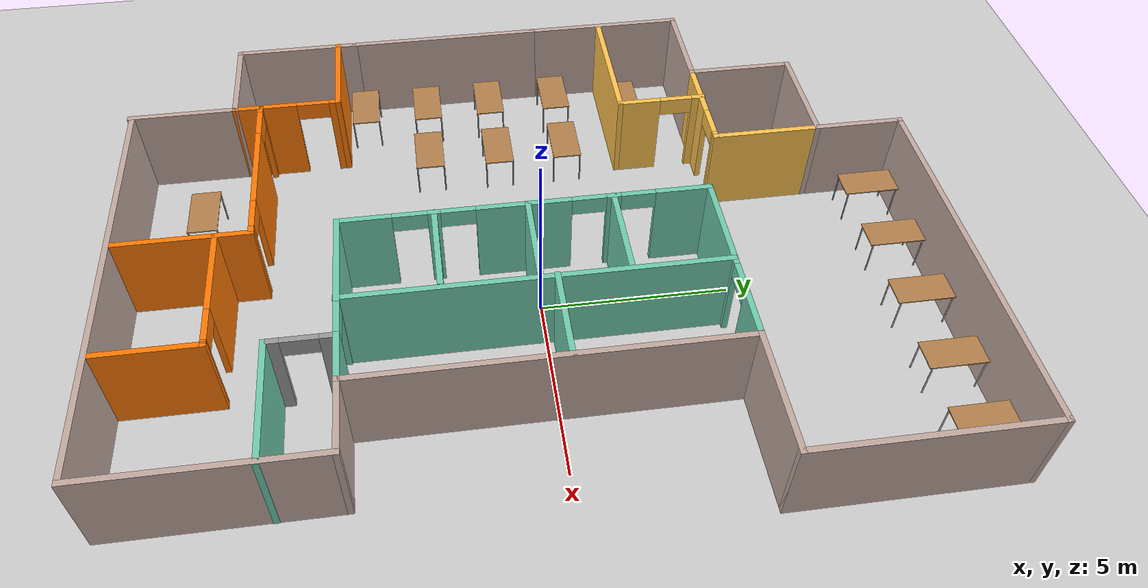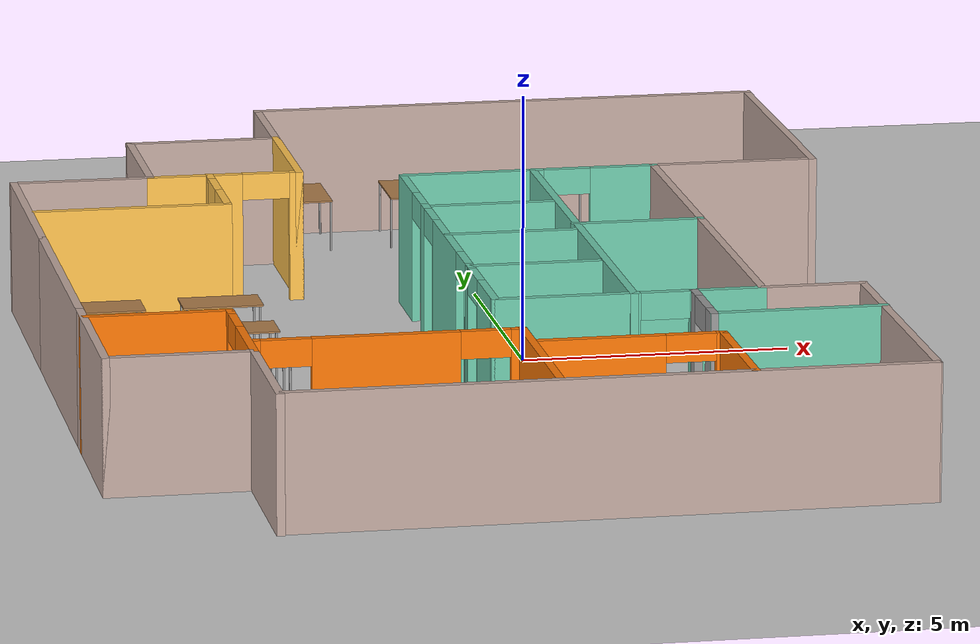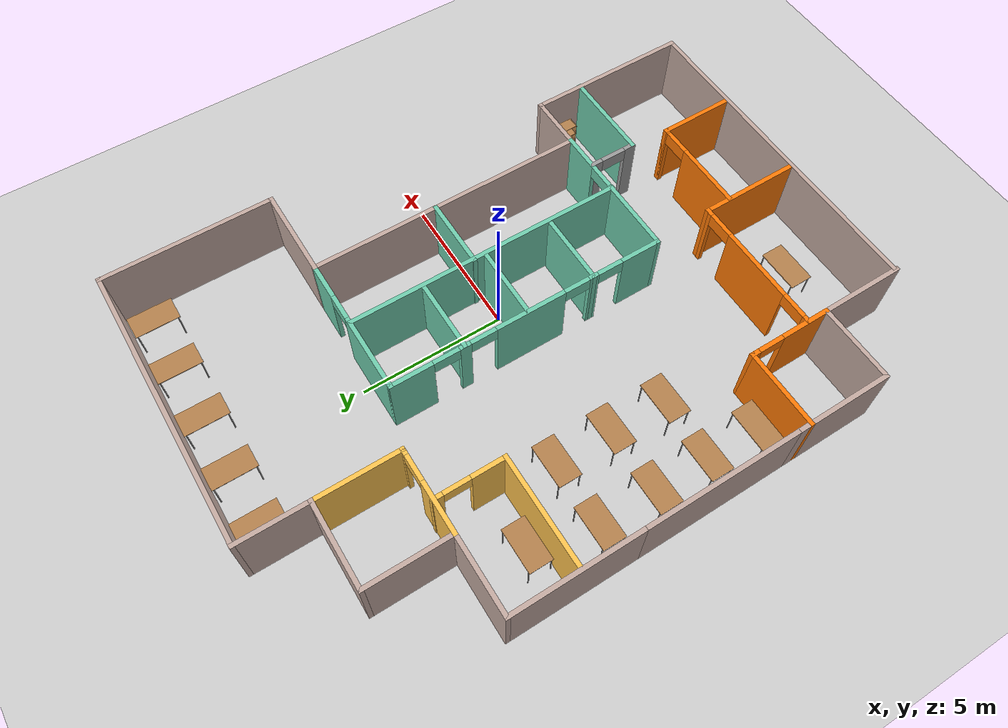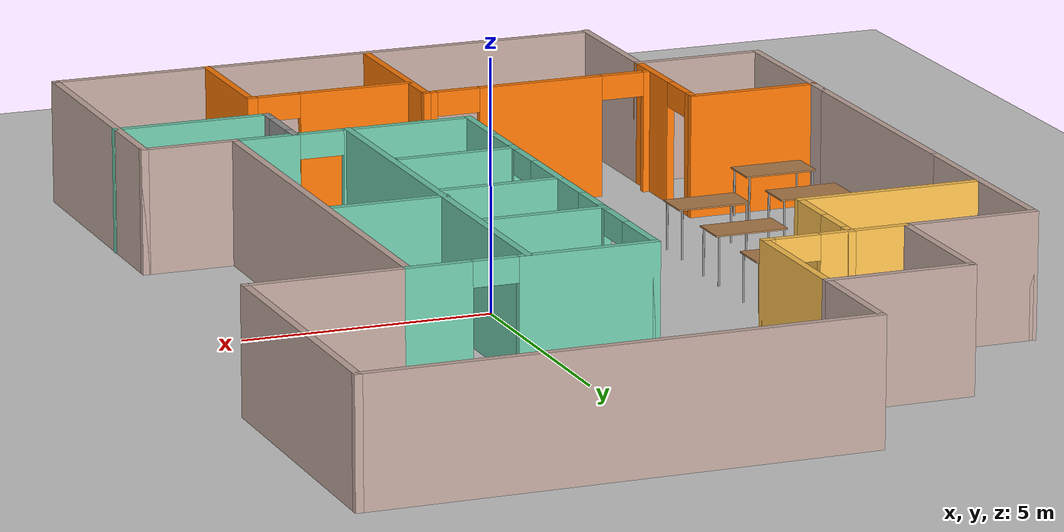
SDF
<sdf version="1.6">
 <world name="default">
  <light name="sun" type="directional">
   <pose>0 0 10 0 -0 0</pose>
   <diffuse>0.8 0.8 0.8 1</diffuse>
   <specular>0.2 0.2 0.2 1</specular>
   <attenuation>
    <range>1000</range>
    <constant>0.9</constant>
    <linear>0.01</linear>
    <quadratic>0.001</quadratic>
   </attenuation>
   <direction>-0.5 0.1 -0.9</direction>
  </light>
  <model name="ground_plane">
   <static>1</static>
   <link name="link">
    <collision name="collision">
     <geometry><plane><normal>0 0 1</normal><size>100 100</size></plane></geometry>
     <surface><friction><ode><mu>100</mu><mu2>50</mu2></ode></friction></surface>
    </collision>
    <visual name="visual">
     <cast_shadows>0</cast_shadows>
     <geometry><plane><normal>0 0 1</normal><size>100 100</size></plane></geometry>
     <material>
      <script><uri>file://media/materials/scripts/gazebo.material</uri><name>Gazebo/Grey</name></script>
     </material>
    </visual>
   </link>
  </model>
  <gravity>0 0 -9.8</gravity>
  <magnetic_field>6e-06 2.3e-05 -4.2e-05</magnetic_field>
  <atmosphere type="adiabatic"/>
  <physics name="default_physics" default="0" type="ode">
   <max_step_size>0.001</max_step_size>
   <real_time_factor>1</real_time_factor>
   <real_time_update_rate>1000</real_time_update_rate>
  </physics>
  <scene><ambient>0.4 0.4 0.4 1</ambient><background>0.7 0.7 0.7 1</background><shadows>1</shadows></scene>
  <spherical_coordinates>
   <surface_model>EARTH_WGS84</surface_model>
   <latitude_deg>0</latitude_deg>
   <longitude_deg>0</longitude_deg>
   <elevation>0</elevation>
   <heading_deg>0</heading_deg>
  </spherical_coordinates>
  <model name="Udacity_L1">
   <pose>-1.15174 -0.093938 0 0 -0 0</pose>
   <link name="Wall_10">
    <collision name="Wall_10_Collision">
     <geometry><box><size>3 0.15 2.5</size></box></geometry>
     <pose>0 0 1.25 0 -0 0</pose>
    </collision>
    <visual name="Wall_10_Visual">
     <pose>0 0 1.25 0 -0 0</pose>
     <geometry><box><size>3 0.15 2.5</size></box></geometry>
     <material>
      <script><uri>file://media/materials/scripts/gazebo.material</uri><name>Gazebo/Grey</name></script>
      <ambient>0.760784 0.662745 0.627451 1</ambient>
     </material>
     <meta><layer>0</layer></meta>
    </visual>
    <pose>-3.625 8.2 0 0 -0 3.14159</pose>
   </link>
   <link name="Wall_11">
    <collision name="Wall_11_Collision">
     <geometry><box><size>3 0.15 2.5</size></box></geometry>
     <pose>0 0 1.25 0 -0 0</pose>
    </collision>
    <visual name="Wall_11_Visual">
     <pose>0 0 1.25 0 -0 0</pose>
     <geometry><box><size>3 0.15 2.5</size></box></geometry>
     <material>
      <script><uri>file://media/materials/scripts/gazebo.material</uri><name>Gazebo/Grey</name></script>
      <ambient>0.760784 0.662745 0.627451 1</ambient>
     </material>
     <meta><layer>0</layer></meta>
    </visual>
    <pose>-5.05 6.775 0 0 0 -1.5708</pose>
   </link>
   <link name="Wall_12">
    <collision name="Wall_12_Collision">
     <geometry><box><size>2.75 0.15 2.5</size></box></geometry>
     <pose>0 0 1.25 0 -0 0</pose>
    </collision>
    <visual name="Wall_12_Visual">
     <pose>0 0 1.25 0 -0 0</pose>
     <geometry><box><size>2.75 0.15 2.5</size></box></geometry>
     <material>
      <script><uri>file://media/materials/scripts/gazebo.material</uri><name>Gazebo/Grey</name></script>
      <ambient>0.760784 0.662745 0.627451 1</ambient>
     </material>
     <meta><layer>0</layer></meta>
    </visual>
    <pose>-6.35 5.35 0 0 -0 3.14159</pose>
   </link>
   <link name="Wall_13">
    <collision name="Wall_13_Collision">
     <geometry><box><size>4.5 0.15 2.5</size></box></geometry>
     <pose>0 0 1.25 0 -0 0</pose>
    </collision>
    <visual name="Wall_13_Visual">
     <pose>0 0 1.25 0 -0 0</pose>
     <geometry><box><size>4.5 0.15 2.5</size></box></geometry>
     <material>
      <script><uri>file://media/materials/scripts/gazebo.material</uri><name>Gazebo/Grey</name></script>
      <ambient>0.760784 0.662745 0.627451 1</ambient>
     </material>
     <meta><layer>0</layer></meta>
    </visual>
    <pose>-7.65 3.175 0 0 0 -1.5708</pose>
   </link>
   <link name="Wall_14">
    <collision name="Wall_14_Collision">
     <geometry><box><size>5.5 0.15 2.5</size></box></geometry>
     <pose>0 0 1.25 0 -0 0</pose>
    </collision>
    <visual name="Wall_14_Visual">
     <pose>0 0 1.25 0 -0 0</pose>
     <geometry><box><size>5.5 0.15 2.5</size></box></geometry>
     <material>
      <script><uri>file://media/materials/scripts/gazebo.material</uri><name>Gazebo/Grey</name></script>
      <ambient>0.760784 0.662745 0.627451 1</ambient>
     </material>
     <meta><layer>0</layer></meta>
    </visual>
    <pose>-7.65 -1.675 0 0 0 -1.5708</pose>
   </link>
   <link name="Wall_15">
    <collision name="Wall_15_Collision">
     <geometry><box><size>3.5 0.15 2.5</size></box></geometry>
     <pose>0 0 1.25 0 -0 0</pose>
    </collision>
    <visual name="Wall_15_Visual">
     <pose>0 0 1.25 0 -0 0</pose>
     <geometry><box><size>3.5 0.15 2.5</size></box></geometry>
     <material>
      <script><uri>file://media/materials/scripts/gazebo.material</uri><name>Gazebo/Grey</name></script>
      <ambient>0.760784 0.662745 0.627451 1</ambient>
     </material>
     <meta><layer>0</layer></meta>
    </visual>
    <pose>-7.65 -6.025 0 0 0 -1.5708</pose>
   </link>
   <link name="Wall_16">
    <collision name="Wall_16_Collision">
     <geometry><box><size>2.75 0.15 2.5</size></box></geometry>
     <pose>0 0 1.25 0 -0 0</pose>
    </collision>
    <visual name="Wall_16_Visual">
     <pose>0 0 1.25 0 -0 0</pose>
     <geometry><box><size>2.75 0.15 2.5</size></box></geometry>
     <material>
      <script><uri>file://media/materials/scripts/gazebo.material</uri><name>Gazebo/Grey</name></script>
      <ambient>0.760784 0.662745 0.627451 1</ambient>
     </material>
     <meta><layer>0</layer></meta>
    </visual>
    <pose>-6.35 -7.7 0 0 -0 0</pose>
   </link>
   <link name="Wall_23">
    <collision name="Wall_23_Collision">
     <geometry><box><size>11.5 0.15 2.5</size></box></geometry>
     <pose>0 0 1.25 0 -0 0</pose>
    </collision>
    <visual name="Wall_23_Visual">
     <pose>0 0 1.25 0 -0 0</pose>
     <geometry><box><size>11.5 0.15 2.5</size></box></geometry>
     <material>
      <script><uri>file://media/materials/scripts/gazebo.material</uri><name>Gazebo/Grey</name></script>
      <ambient>0.760784 0.662745 0.627451 1</ambient>
     </material>
     <meta><layer>0</layer></meta>
    </visual>
    <pose>0.6984 -10.5 0 0 -0 3.14159</pose>
   </link>
   <link name="Wall_25">
    <collision name="Wall_25_Collision">
     <geometry><box><size>3 0.15 2.5</size></box></geometry>
     <pose>0 0 1.25 0 -0 0</pose>
    </collision>
    <visual name="Wall_25_Visual">
     <pose>0 0 1.25 0 -0 0</pose>
     <geometry><box><size>3 0.15 2.5</size></box></geometry>
     <material>
      <script><uri>file://media/materials/scripts/gazebo.material</uri><name>Gazebo/Grey</name></script>
      <ambient>0.760784 0.662745 0.627451 1</ambient>
     </material>
     <meta><layer>0</layer></meta>
    </visual>
    <pose>-5.05 -9.125 0 0 0 -1.5708</pose>
   </link>
   <link name="Wall_27">
    <pose>-3.625 5.35 0 0 -0 0</pose>
    <visual name="Wall_27_Visual_0">
     <pose>-0.583933 0 1.25 0 -0 0</pose>
     <geometry><box><size>1.83213 0.15 2.5</size></box></geometry>
     <material>
      <script><uri>file://media/materials/scripts/gazebo.material</uri><name>Gazebo/Grey</name></script>
      <ambient>1 0.764706 0.305882 1</ambient>
     </material>
     <meta><layer>0</layer></meta>
    </visual>
    <collision name="Wall_27_Collision_0">
     <geometry><box><size>1.83213 0.15 2.5</size></box></geometry>
     <pose>-0.583933 0 1.25 0 -0 0</pose>
    </collision>
    <visual name="Wall_27_Visual_1">
     <pose>1.36607 0 1.25 0 -0 0</pose>
     <geometry><box><size>0.267866 0.15 2.5</size></box></geometry>
     <material>
      <script><uri>file://media/materials/scripts/gazebo.material</uri><name>Gazebo/Grey</name></script>
      <ambient>1 0.764706 0.305882 1</ambient>
     </material>
     <meta><layer>0</layer></meta>
    </visual>
    <collision name="Wall_27_Collision_1">
     <geometry><box><size>0.267866 0.15 2.5</size></box></geometry>
     <pose>1.36607 0 1.25 0 -0 0</pose>
    </collision>
    <visual name="Wall_27_Visual_2">
     <pose>0.782134 0 2.25 0 -0 0</pose>
     <geometry><box><size>0.9 0.15 0.5</size></box></geometry>
     <material>
      <script><uri>file://media/materials/scripts/gazebo.material</uri><name>Gazebo/Grey</name></script>
      <ambient>1 0.764706 0.305882 1</ambient>
     </material>
     <meta><layer>0</layer></meta>
    </visual>
    <collision name="Wall_27_Collision_2">
     <geometry><box><size>0.9 0.15 0.5</size></box></geometry>
     <pose>0.782134 0 2.25 0 -0 0</pose>
    </collision>
   </link>
   <link name="Wall_28">
    <collision name="Wall_28_Collision">
     <geometry><box><size>3 0.15 2.5</size></box></geometry>
     <pose>0 0 1.25 0 -0 0</pose>
    </collision>
    <visual name="Wall_28_Visual">
     <pose>0 0 1.25 0 -0 0</pose>
     <geometry><box><size>3 0.15 2.5</size></box></geometry>
     <material>
      <script><uri>file://media/materials/scripts/gazebo.material</uri><name>Gazebo/Grey</name></script>
      <ambient>1 0.764706 0.305882 1</ambient>
     </material>
     <meta><layer>0</layer></meta>
    </visual>
    <pose>-2.2 6.775 0 0 -0 1.5708</pose>
   </link>
   <link name="Wall_3">
    <collision name="Wall_3_Collision">
     <geometry><box><size>5.75 0.15 2.5</size></box></geometry>
     <pose>0 0 1.25 0 -0 0</pose>
    </collision>
    <visual name="Wall_3_Visual">
     <pose>0 0 1.25 0 -0 0</pose>
     <geometry><box><size>5.75 0.15 2.5</size></box></geometry>
     <material>
      <script><uri>file://media/materials/scripts/gazebo.material</uri><name>Gazebo/Grey</name></script>
      <ambient>0.760784 0.662745 0.627451 1</ambient>
     </material>
     <meta><layer>0</layer></meta>
    </visual>
    <pose>6.4 -7.7 0 0 -0 1.5708</pose>
   </link>
   <link name="Wall_33">
    <pose>-3.91607 4.20045 0 0 0 -1.5708</pose>
    <visual name="Wall_33_Visual_0">
     <pose>-1.05923 0 1.25 0 -0 0</pose>
     <geometry><box><size>0.381547 0.15 2.5</size></box></geometry>
     <material>
      <script><uri>file://media/materials/scripts/gazebo.material</uri><name>Gazebo/Grey</name></script>
      <ambient>1 0.764706 0.305882 1</ambient>
     </material>
     <meta><layer>0</layer></meta>
    </visual>
    <collision name="Wall_33_Collision_0">
     <geometry><box><size>0.381547 0.15 2.5</size></box></geometry>
     <pose>-1.05923 0 1.25 0 -0 0</pose>
    </collision>
    <visual name="Wall_33_Visual_1">
     <pose>0.640774 0 1.25 0 -0 0</pose>
     <geometry><box><size>1.21845 0.15 2.5</size></box></geometry>
     <material>
      <script><uri>file://media/materials/scripts/gazebo.material</uri><name>Gazebo/Grey</name></script>
      <ambient>1 0.764706 0.305882 1</ambient>
     </material>
     <meta><layer>0</layer></meta>
    </visual>
    <collision name="Wall_33_Collision_1">
     <geometry><box><size>1.21845 0.15 2.5</size></box></geometry>
     <pose>0.640774 0 1.25 0 -0 0</pose>
    </collision>
    <visual name="Wall_33_Visual_2">
     <pose>-0.418453 0 2.25 0 -0 0</pose>
     <geometry><box><size>0.9 0.15 0.5</size></box></geometry>
     <material>
      <script><uri>file://media/materials/scripts/gazebo.material</uri><name>Gazebo/Grey</name></script>
      <ambient>1 0.764706 0.305882 1</ambient>
     </material>
     <meta><layer>0</layer></meta>
    </visual>
    <collision name="Wall_33_Collision_2">
     <geometry><box><size>0.9 0.15 0.5</size></box></geometry>
     <pose>-0.418453 0 2.25 0 -0 0</pose>
    </collision>
   </link>
   <link name="Wall_34">
    <collision name="Wall_34_Collision">
     <geometry><box><size>3.75 0.15 2.5</size></box></geometry>
     <pose>0 0 1.25 0 -0 0</pose>
    </collision>
    <visual name="Wall_34_Visual">
     <pose>0 0 1.25 0 -0 0</pose>
     <geometry><box><size>3.75 0.15 2.5</size></box></geometry>
     <material>
      <script><uri>file://media/materials/scripts/gazebo.material</uri><name>Gazebo/Grey</name></script>
      <ambient>1 0.764706 0.305882 1</ambient>
     </material>
     <meta><layer>0</layer></meta>
    </visual>
    <pose>-5.71607 3.02545 0 0 -0 3.14159</pose>
   </link>
   <link name="Wall_36">
    <pose>-5.05 -6.275 0 0 -0 1.5708</pose>
    <visual name="Wall_36_Visual_0">
     <pose>-0.615418 0 1.25 0 -0 0</pose>
     <geometry><box><size>1.76916 0.15 2.5</size></box></geometry>
     <material>
      <script><uri>file://media/materials/scripts/gazebo.material</uri><name>Gazebo/Grey</name></script>
      <ambient>0.996078 0.47451 0.0196078 1</ambient>
     </material>
     <meta><layer>0</layer></meta>
    </visual>
    <collision name="Wall_36_Collision_0">
     <geometry><box><size>1.76916 0.15 2.5</size></box></geometry>
     <pose>-0.615418 0 1.25 0 -0 0</pose>
    </collision>
    <visual name="Wall_36_Visual_1">
     <pose>1.33458 0 1.25 0 -0 0</pose>
     <geometry><box><size>0.330836 0.15 2.5</size></box></geometry>
     <material>
      <script><uri>file://media/materials/scripts/gazebo.material</uri><name>Gazebo/Grey</name></script>
      <ambient>0.996078 0.47451 0.0196078 1</ambient>
     </material>
     <meta><layer>0</layer></meta>
    </visual>
    <collision name="Wall_36_Collision_1">
     <geometry><box><size>0.330836 0.15 2.5</size></box></geometry>
     <pose>1.33458 0 1.25 0 -0 0</pose>
    </collision>
    <visual name="Wall_36_Visual_2">
     <pose>0.719164 0 2.25 0 -0 0</pose>
     <geometry><box><size>0.9 0.15 0.5</size></box></geometry>
     <material>
      <script><uri>file://media/materials/scripts/gazebo.material</uri><name>Gazebo/Grey</name></script>
      <ambient>0.996078 0.47451 0.0196078 1</ambient>
     </material>
     <meta><layer>0</layer></meta>
    </visual>
    <collision name="Wall_36_Collision_2">
     <geometry><box><size>0.9 0.15 0.5</size></box></geometry>
     <pose>0.719164 0 2.25 0 -0 0</pose>
    </collision>
   </link>
   <link name="Wall_37">
    <collision name="Wall_37_Collision">
     <geometry><box><size>2.75 0.15 2.5</size></box></geometry>
     <pose>0 0 1.25 0 -0 0</pose>
    </collision>
    <visual name="Wall_37_Visual">
     <pose>0 0 1.25 0 -0 0</pose>
     <geometry><box><size>2.75 0.15 2.5</size></box></geometry>
     <material>
      <script><uri>file://media/materials/scripts/gazebo.material</uri><name>Gazebo/Grey</name></script>
      <ambient>0.996078 0.47451 0.0196078 1</ambient>
     </material>
     <meta><layer>0</layer></meta>
    </visual>
    <pose>-6.35 -4.85 0 0 -0 3.14159</pose>
   </link>
   <link name="Wall_39">
    <pose>-2.61929 -7.0035 0 0 -0 0</pose>
    <visual name="Wall_39_Visual_0">
     <pose>-2.36162 0 1.25 0 -0 0</pose>
     <geometry><box><size>0.27676 0.15 2.5</size></box></geometry>
     <material>
      <script><uri>file://media/materials/scripts/gazebo.material</uri><name>Gazebo/Grey</name></script>
      <ambient>0.996078 0.47451 0.0196078 1</ambient>
     </material>
     <meta><layer>0</layer></meta>
    </visual>
    <collision name="Wall_39_Collision_0">
     <geometry><box><size>0.27676 0.15 2.5</size></box></geometry>
     <pose>-2.36162 0 1.25 0 -0 0</pose>
    </collision>
    <visual name="Wall_39_Visual_1">
     <pose>-0.007702 0 1.25 0 -0 0</pose>
     <geometry><box><size>2.63108 0.15 2.5</size></box></geometry>
     <material>
      <script><uri>file://media/materials/scripts/gazebo.material</uri><name>Gazebo/Grey</name></script>
      <ambient>0.996078 0.47451 0.0196078 1</ambient>
     </material>
     <meta><layer>0</layer></meta>
    </visual>
    <collision name="Wall_39_Collision_1">
     <geometry><box><size>2.63108 0.15 2.5</size></box></geometry>
     <pose>-0.007702 0 1.25 0 -0 0</pose>
    </collision>
    <visual name="Wall_39_Visual_2">
     <pose>2.35392 0 1.25 0 -0 0</pose>
     <geometry><box><size>0.292165 0.15 2.5</size></box></geometry>
     <material>
      <script><uri>file://media/materials/scripts/gazebo.material</uri><name>Gazebo/Grey</name></script>
      <ambient>0.996078 0.47451 0.0196078 1</ambient>
     </material>
     <meta><layer>0</layer></meta>
    </visual>
    <collision name="Wall_39_Collision_2">
     <geometry><box><size>0.292165 0.15 2.5</size></box></geometry>
     <pose>2.35392 0 1.25 0 -0 0</pose>
    </collision>
    <visual name="Wall_39_Visual_3">
     <pose>-1.77324 0 2.25 0 -0 0</pose>
     <geometry><box><size>0.9 0.15 0.5</size></box></geometry>
     <material>
      <script><uri>file://media/materials/scripts/gazebo.material</uri><name>Gazebo/Grey</name></script>
      <ambient>0.996078 0.47451 0.0196078 1</ambient>
     </material>
     <meta><layer>0</layer></meta>
    </visual>
    <collision name="Wall_39_Collision_3">
     <geometry><box><size>0.9 0.15 0.5</size></box></geometry>
     <pose>-1.77324 0 2.25 0 -0 0</pose>
    </collision>
    <visual name="Wall_39_Visual_4">
     <pose>1.75784 0 2.25 0 -0 0</pose>
     <geometry><box><size>0.9 0.15 0.5</size></box></geometry>
     <material>
      <script><uri>file://media/materials/scripts/gazebo.material</uri><name>Gazebo/Grey</name></script>
      <ambient>0.996078 0.47451 0.0196078 1</ambient>
     </material>
     <meta><layer>0</layer></meta>
    </visual>
    <collision name="Wall_39_Collision_4">
     <geometry><box><size>0.9 0.15 0.5</size></box></geometry>
     <pose>1.75784 0 2.25 0 -0 0</pose>
    </collision>
   </link>
   <link name="Wall_4">
    <collision name="Wall_4_Collision">
     <geometry><box><size>2 0.15 2.5</size></box></geometry>
     <pose>0 0 1.25 0 -0 0</pose>
    </collision>
    <visual name="Wall_4_Visual">
     <pose>0 0 1.25 0 -0 0</pose>
     <geometry><box><size>2 0.15 2.5</size></box></geometry>
     <material>
      <script><uri>file://media/materials/scripts/gazebo.material</uri><name>Gazebo/Grey</name></script>
      <ambient>0.760784 0.662745 0.627451 1</ambient>
     </material>
     <meta><layer>0</layer></meta>
    </visual>
    <pose>5.475 -4.9 0 0 -0 3.14159</pose>
   </link>
   <link name="Wall_40">
    <collision name="Wall_40_Collision">
     <geometry><box><size>3.5 0.15 2.5</size></box></geometry>
     <pose>0 0 1.25 0 -0 0</pose>
    </collision>
    <visual name="Wall_40_Visual">
     <pose>0 0 1.25 0 -0 0</pose>
     <geometry><box><size>3.5 0.15 2.5</size></box></geometry>
     <material>
      <script><uri>file://media/materials/scripts/gazebo.material</uri><name>Gazebo/Grey</name></script>
      <ambient>0.996078 0.47451 0.0196078 1</ambient>
     </material>
     <meta><layer>0</layer></meta>
    </visual>
    <pose>-0.194292 -8.67849 0 0 0 -1.5708</pose>
   </link>
   <link name="Wall_42">
    <pose>1.52514 -7.8813 0 0 -0 0</pose>
    <visual name="Wall_42_Visual_0">
     <pose>-0.554213 0 1.25 0 -0 0</pose>
     <geometry><box><size>2.39157 0.15 2.5</size></box></geometry>
     <material>
      <script><uri>file://media/materials/scripts/gazebo.material</uri><name>Gazebo/Grey</name></script>
      <ambient>0.996078 0.47451 0.0196078 1</ambient>
     </material>
     <meta><layer>0</layer></meta>
    </visual>
    <collision name="Wall_42_Collision_0">
     <geometry><box><size>2.39157 0.15 2.5</size></box></geometry>
     <pose>-0.554213 0 1.25 0 -0 0</pose>
    </collision>
    <visual name="Wall_42_Visual_1">
     <pose>1.64579 0 1.25 0 -0 0</pose>
     <geometry><box><size>0.208426 0.15 2.5</size></box></geometry>
     <material>
      <script><uri>file://media/materials/scripts/gazebo.material</uri><name>Gazebo/Grey</name></script>
      <ambient>0.996078 0.47451 0.0196078 1</ambient>
     </material>
     <meta><layer>0</layer></meta>
    </visual>
    <collision name="Wall_42_Collision_1">
     <geometry><box><size>0.208426 0.15 2.5</size></box></geometry>
     <pose>1.64579 0 1.25 0 -0 0</pose>
    </collision>
    <visual name="Wall_42_Visual_2">
     <pose>1.09157 0 2.25 0 -0 0</pose>
     <geometry><box><size>0.9 0.15 0.5</size></box></geometry>
     <material>
      <script><uri>file://media/materials/scripts/gazebo.material</uri><name>Gazebo/Grey</name></script>
      <ambient>0.996078 0.47451 0.0196078 1</ambient>
     </material>
     <meta><layer>0</layer></meta>
    </visual>
    <collision name="Wall_42_Collision_2">
     <geometry><box><size>0.9 0.15 0.5</size></box></geometry>
     <pose>1.09157 0 2.25 0 -0 0</pose>
    </collision>
   </link>
   <link name="Wall_43">
    <collision name="Wall_43_Collision">
     <geometry><box><size>2.75 0.15 2.5</size></box></geometry>
     <pose>0 0 1.25 0 -0 0</pose>
    </collision>
    <visual name="Wall_43_Visual">
     <pose>0 0 1.25 0 -0 0</pose>
     <geometry><box><size>2.75 0.15 2.5</size></box></geometry>
     <material>
      <script><uri>file://media/materials/scripts/gazebo.material</uri><name>Gazebo/Grey</name></script>
      <ambient>0.996078 0.47451 0.0196078 1</ambient>
     </material>
     <meta><layer>0</layer></meta>
    </visual>
    <pose>3.20015 -9.1813 0 0 0 -1.5708</pose>
   </link>
   <link name="Wall_48">
    <pose>2.125 -4.9 0 0 -0 3.14159</pose>
    <visual name="Wall_48_Visual_0">
     <pose>-1.80048 0 1.25 0 -0 0</pose>
     <geometry><box><size>1.39905 0.15 2.5</size></box></geometry>
     <material>
      <script><uri>file://media/materials/scripts/gazebo.material</uri><name>Gazebo/Grey</name></script>
      <ambient>0.435294 0.796078 0.67451 1</ambient>
     </material>
     <meta><layer>0</layer></meta>
    </visual>
    <collision name="Wall_48_Collision_0">
     <geometry><box><size>1.39905 0.15 2.5</size></box></geometry>
     <pose>-1.80048 0 1.25 0 -0 0</pose>
    </collision>
    <visual name="Wall_48_Visual_1">
     <pose>1.14952 0 1.25 0 -0 0</pose>
     <geometry><box><size>2.70095 0.15 2.5</size></box></geometry>
     <material>
      <script><uri>file://media/materials/scripts/gazebo.material</uri><name>Gazebo/Grey</name></script>
      <ambient>0.435294 0.796078 0.67451 1</ambient>
     </material>
     <meta><layer>0</layer></meta>
    </visual>
    <collision name="Wall_48_Collision_1">
     <geometry><box><size>2.70095 0.15 2.5</size></box></geometry>
     <pose>1.14952 0 1.25 0 -0 0</pose>
    </collision>
    <visual name="Wall_48_Visual_2">
     <pose>-0.65095 0 2.25 0 -0 0</pose>
     <geometry><box><size>0.9 0.15 0.5</size></box></geometry>
     <material>
      <script><uri>file://media/materials/scripts/gazebo.material</uri><name>Gazebo/Grey</name></script>
      <ambient>0.435294 0.796078 0.67451 1</ambient>
     </material>
     <meta><layer>0</layer></meta>
    </visual>
    <collision name="Wall_48_Collision_2">
     <geometry><box><size>0.9 0.15 0.5</size></box></geometry>
     <pose>-0.65095 0 2.25 0 -0 0</pose>
    </collision>
   </link>
   <link name="Wall_49">
    <pose>-0.3 -0.1 0 0 -0 1.5708</pose>
    <visual name="Wall_49_Visual_0">
     <pose>-4.1449 0 1.25 0 -0 0</pose>
     <geometry><box><size>1.46019 0.15 2.5</size></box></geometry>
     <material>
      <script><uri>file://media/materials/scripts/gazebo.material</uri><name>Gazebo/Grey</name></script>
      <ambient>0.435294 0.796078 0.67451 1</ambient>
     </material>
     <meta><layer>0</layer></meta>
    </visual>
    <collision name="Wall_49_Collision_0">
     <geometry><box><size>1.46019 0.15 2.5</size></box></geometry>
     <pose>-4.1449 0 1.25 0 -0 0</pose>
    </collision>
    <visual name="Wall_49_Visual_1">
     <pose>-2.34984 0 1.25 0 -0 0</pose>
     <geometry><box><size>0.329925 0.15 2.5</size></box></geometry>
     <material>
      <script><uri>file://media/materials/scripts/gazebo.material</uri><name>Gazebo/Grey</name></script>
      <ambient>0.435294 0.796078 0.67451 1</ambient>
     </material>
     <meta><layer>0</layer></meta>
    </visual>
    <collision name="Wall_49_Collision_1">
     <geometry><box><size>0.329925 0.15 2.5</size></box></geometry>
     <pose>-2.34984 0 1.25 0 -0 0</pose>
    </collision>
    <visual name="Wall_49_Visual_2">
     <pose>-0.048692 0 1.25 0 -0 0</pose>
     <geometry><box><size>2.47237 0.15 2.5</size></box></geometry>
     <material>
      <script><uri>file://media/materials/scripts/gazebo.material</uri><name>Gazebo/Grey</name></script>
      <ambient>0.435294 0.796078 0.67451 1</ambient>
     </material>
     <meta><layer>0</layer></meta>
    </visual>
    <collision name="Wall_49_Collision_2">
     <geometry><box><size>2.47237 0.15 2.5</size></box></geometry>
     <pose>-0.048692 0 1.25 0 -0 0</pose>
    </collision>
    <visual name="Wall_49_Visual_3">
     <pose>2.27891 0 1.25 0 -0 0</pose>
     <geometry><box><size>0.382825 0.15 2.5</size></box></geometry>
     <material>
      <script><uri>file://media/materials/scripts/gazebo.material</uri><name>Gazebo/Grey</name></script>
      <ambient>0.435294 0.796078 0.67451 1</ambient>
     </material>
     <meta><layer>0</layer></meta>
    </visual>
    <collision name="Wall_49_Collision_3">
     <geometry><box><size>0.382825 0.15 2.5</size></box></geometry>
     <pose>2.27891 0 1.25 0 -0 0</pose>
    </collision>
    <visual name="Wall_49_Visual_4">
     <pose>4.12266 0 1.25 0 -0 0</pose>
     <geometry><box><size>1.50468 0.15 2.5</size></box></geometry>
     <material>
      <script><uri>file://media/materials/scripts/gazebo.material</uri><name>Gazebo/Grey</name></script>
      <ambient>0.435294 0.796078 0.67451 1</ambient>
     </material>
     <meta><layer>0</layer></meta>
    </visual>
    <collision name="Wall_49_Collision_4">
     <geometry><box><size>1.50468 0.15 2.5</size></box></geometry>
     <pose>4.12266 0 1.25 0 -0 0</pose>
    </collision>
    <visual name="Wall_49_Visual_5">
     <pose>-2.96481 0 2.25 0 -0 0</pose>
     <geometry><box><size>0.9 0.15 0.5</size></box></geometry>
     <material>
      <script><uri>file://media/materials/scripts/gazebo.material</uri><name>Gazebo/Grey</name></script>
      <ambient>0.435294 0.796078 0.67451 1</ambient>
     </material>
     <meta><layer>0</layer></meta>
    </visual>
    <collision name="Wall_49_Collision_5">
     <geometry><box><size>0.9 0.15 0.5</size></box></geometry>
     <pose>-2.96481 0 2.25 0 -0 0</pose>
    </collision>
    <visual name="Wall_49_Visual_6">
     <pose>-1.73488 0 2.25 0 -0 0</pose>
     <geometry><box><size>0.9 0.15 0.5</size></box></geometry>
     <material>
      <script><uri>file://media/materials/scripts/gazebo.material</uri><name>Gazebo/Grey</name></script>
      <ambient>0.435294 0.796078 0.67451 1</ambient>
     </material>
     <meta><layer>0</layer></meta>
    </visual>
    <collision name="Wall_49_Collision_6">
     <geometry><box><size>0.9 0.15 0.5</size></box></geometry>
     <pose>-1.73488 0 2.25 0 -0 0</pose>
    </collision>
    <visual name="Wall_49_Visual_7">
     <pose>1.63749 0 2.25 0 -0 0</pose>
     <geometry><box><size>0.9 0.15 0.5</size></box></geometry>
     <material>
      <script><uri>file://media/materials/scripts/gazebo.material</uri><name>Gazebo/Grey</name></script>
      <ambient>0.435294 0.796078 0.67451 1</ambient>
     </material>
     <meta><layer>0</layer></meta>
    </visual>
    <collision name="Wall_49_Collision_7">
     <geometry><box><size>0.9 0.15 0.5</size></box></geometry>
     <pose>1.63749 0 2.25 0 -0 0</pose>
    </collision>
    <visual name="Wall_49_Visual_8">
     <pose>2.92032 0 2.25 0 -0 0</pose>
     <geometry><box><size>0.9 0.15 0.5</size></box></geometry>
     <material>
      <script><uri>file://media/materials/scripts/gazebo.material</uri><name>Gazebo/Grey</name></script>
      <ambient>0.435294 0.796078 0.67451 1</ambient>
     </material>
     <meta><layer>0</layer></meta>
    </visual>
    <collision name="Wall_49_Collision_8">
     <geometry><box><size>0.9 0.15 0.5</size></box></geometry>
     <pose>2.92032 0 2.25 0 -0 0</pose>
    </collision>
   </link>
   <link name="Wall_5">
    <collision name="Wall_5_Collision">
     <geometry><box><size>9.75 0.15 2.5</size></box></geometry>
     <pose>0 0 1.25 0 -0 0</pose>
    </collision>
    <visual name="Wall_5_Visual">
     <pose>0 0 1.25 0 -0 0</pose>
     <geometry><box><size>9.75 0.15 2.5</size></box></geometry>
     <material>
      <script><uri>file://media/materials/scripts/gazebo.material</uri><name>Gazebo/Grey</name></script>
      <ambient>0.760784 0.662745 0.627451 1</ambient>
     </material>
     <meta><layer>0</layer></meta>
    </visual>
    <pose>4.55 -0.1 0 0 -0 1.5708</pose>
   </link>
   <link name="Wall_50">
    <pose>2.125 4.7 0 0 -0 0</pose>
    <visual name="Wall_50_Visual_0">
     <pose>-1.10811 0 1.25 0 -0 0</pose>
     <geometry><box><size>2.78378 0.15 2.5</size></box></geometry>
     <material>
      <script><uri>file://media/materials/scripts/gazebo.material</uri><name>Gazebo/Grey</name></script>
      <ambient>0.435294 0.796078 0.67451 1</ambient>
     </material>
     <meta><layer>0</layer></meta>
    </visual>
    <collision name="Wall_50_Collision_0">
     <geometry><box><size>2.78378 0.15 2.5</size></box></geometry>
     <pose>-1.10811 0 1.25 0 -0 0</pose>
    </collision>
    <visual name="Wall_50_Visual_1">
     <pose>1.84189 0 1.25 0 -0 0</pose>
     <geometry><box><size>1.31622 0.15 2.5</size></box></geometry>
     <material>
      <script><uri>file://media/materials/scripts/gazebo.material</uri><name>Gazebo/Grey</name></script>
      <ambient>0.435294 0.796078 0.67451 1</ambient>
     </material>
     <meta><layer>0</layer></meta>
    </visual>
    <collision name="Wall_50_Collision_1">
     <geometry><box><size>1.31622 0.15 2.5</size></box></geometry>
     <pose>1.84189 0 1.25 0 -0 0</pose>
    </collision>
    <visual name="Wall_50_Visual_2">
     <pose>0.733778 0 2.25 0 -0 0</pose>
     <geometry><box><size>0.9 0.15 0.5</size></box></geometry>
     <material>
      <script><uri>file://media/materials/scripts/gazebo.material</uri><name>Gazebo/Grey</name></script>
      <ambient>0.435294 0.796078 0.67451 1</ambient>
     </material>
     <meta><layer>0</layer></meta>
    </visual>
    <collision name="Wall_50_Collision_2">
     <geometry><box><size>0.9 0.15 0.5</size></box></geometry>
     <pose>0.733778 0 2.25 0 -0 0</pose>
    </collision>
   </link>
   <link name="Wall_55">
    <pose>3.31562 -5.73776 0 0 0 -1.5708</pose>
    <visual name="Wall_55_Visual_0">
     <pose>-0.662812 0 1.25 0 -0 0</pose>
     <geometry><box><size>0.424377 0.15 2.5</size></box></geometry>
     <material>
      <script><uri>file://media/materials/scripts/gazebo.material</uri><name>Gazebo/Grey</name></script>
      <ambient>1 1 1 1</ambient>
     </material>
     <meta><layer>0</layer></meta>
    </visual>
    <collision name="Wall_55_Collision_0">
     <geometry><box><size>0.424377 0.15 2.5</size></box></geometry>
     <pose>-0.662812 0 1.25 0 -0 0</pose>
    </collision>
    <visual name="Wall_55_Visual_1">
     <pose>0.662188 0 1.25 0 -0 0</pose>
     <geometry><box><size>0.425623 0.15 2.5</size></box></geometry>
     <material>
      <script><uri>file://media/materials/scripts/gazebo.material</uri><name>Gazebo/Grey</name></script>
      <ambient>1 1 1 1</ambient>
     </material>
     <meta><layer>0</layer></meta>
    </visual>
    <collision name="Wall_55_Collision_1">
     <geometry><box><size>0.425623 0.15 2.5</size></box></geometry>
     <pose>0.662188 0 1.25 0 -0 0</pose>
    </collision>
    <visual name="Wall_55_Visual_2">
     <pose>-0.000623 0 2.25 0 -0 0</pose>
     <geometry><box><size>0.9 0.15 0.5</size></box></geometry>
     <material>
      <script><uri>file://media/materials/scripts/gazebo.material</uri><name>Gazebo/Grey</name></script>
      <ambient>1 1 1 1</ambient>
     </material>
     <meta><layer>0</layer></meta>
    </visual>
    <collision name="Wall_55_Collision_2">
     <geometry><box><size>0.9 0.15 0.5</size></box></geometry>
     <pose>-0.000623 0 2.25 0 -0 0</pose>
    </collision>
   </link>
   <link name="Wall_56">
    <collision name="Wall_56_Collision">
     <geometry><box><size>3.25 0.15 2.5</size></box></geometry>
     <pose>0 0 1.25 0 -0 0</pose>
    </collision>
    <visual name="Wall_56_Visual">
     <pose>0 0 1.25 0 -0 0</pose>
     <geometry><box><size>3.25 0.15 2.5</size></box></geometry>
     <material>
      <script><uri>file://media/materials/scripts/gazebo.material</uri><name>Gazebo/Grey</name></script>
      <ambient>0.435294 0.796078 0.67451 1</ambient>
     </material>
     <meta><layer>0</layer></meta>
    </visual>
    <pose>4.86562 -6.53776 0 0 -0 0</pose>
   </link>
   <link name="Wall_58">
    <collision name="Wall_58_Collision">
     <geometry><box><size>9.75 0.15 2.5</size></box></geometry>
     <pose>0 0 1.25 0 -0 0</pose>
    </collision>
    <visual name="Wall_58_Visual">
     <pose>0 0 1.25 0 -0 0</pose>
     <geometry><box><size>9.75 0.15 2.5</size></box></geometry>
     <material>
      <script><uri>file://media/materials/scripts/gazebo.material</uri><name>Gazebo/Grey</name></script>
      <ambient>0.435294 0.796078 0.67451 1</ambient>
     </material>
     <meta><layer>0</layer></meta>
    </visual>
    <pose>2.20765 -0.117521 0 0 -0 1.5708</pose>
   </link>
   <link name="Wall_6">
    <collision name="Wall_6_Collision">
     <geometry><box><size>3.25 0.15 2.5</size></box></geometry>
     <pose>0 0 1.25 0 -0 0</pose>
    </collision>
    <visual name="Wall_6_Visual">
     <pose>0 0 1.25 0 -0 0</pose>
     <geometry><box><size>3.25 0.15 2.5</size></box></geometry>
     <material>
      <script><uri>file://media/materials/scripts/gazebo.material</uri><name>Gazebo/Grey</name></script>
      <ambient>0.760784 0.662745 0.627451 1</ambient>
     </material>
     <meta><layer>0</layer></meta>
    </visual>
    <pose>6.1 4.7 0 0 -0 0</pose>
   </link>
   <link name="Wall_60">
    <collision name="Wall_60_Collision">
     <geometry><box><size>2.5 0.15 2.5</size></box></geometry>
     <pose>0 0 1.25 0 -0 0</pose>
    </collision>
    <visual name="Wall_60_Visual">
     <pose>0 0 1.25 0 -0 0</pose>
     <geometry><box><size>2.5 0.15 2.5</size></box></geometry>
     <material>
      <script><uri>file://media/materials/scripts/gazebo.material</uri><name>Gazebo/Grey</name></script>
      <ambient>0.435294 0.796078 0.67451 1</ambient>
     </material>
     <meta><layer>0</layer></meta>
    </visual>
    <pose>3.35522 0.356501 0 0 -0 0</pose>
   </link>
   <link name="Wall_62">
    <collision name="Wall_62_Collision">
     <geometry><box><size>2.5 0.15 2.5</size></box></geometry>
     <pose>0 0 1.25 0 -0 0</pose>
    </collision>
    <visual name="Wall_62_Visual">
     <pose>0 0 1.25 0 -0 0</pose>
     <geometry><box><size>2.5 0.15 2.5</size></box></geometry>
     <material>
      <script><uri>file://media/materials/scripts/gazebo.material</uri><name>Gazebo/Grey</name></script>
      <ambient>0.435294 0.796078 0.67451 1</ambient>
     </material>
     <meta><layer>0</layer></meta>
    </visual>
    <pose>0.868807 -2.44775 0 0 -0 0</pose>
   </link>
   <link name="Wall_64">
    <collision name="Wall_64_Collision">
     <geometry><box><size>2.5 0.15 2.5</size></box></geometry>
     <pose>0 0 1.25 0 -0 0</pose>
    </collision>
    <visual name="Wall_64_Visual">
     <pose>0 0 1.25 0 -0 0</pose>
     <geometry><box><size>2.5 0.15 2.5</size></box></geometry>
     <material>
      <script><uri>file://media/materials/scripts/gazebo.material</uri><name>Gazebo/Grey</name></script>
      <ambient>0.435294 0.796078 0.67451 1</ambient>
     </material>
     <meta><layer>0</layer></meta>
    </visual>
    <pose>0.902752 -0.053917 0 0 -0 0</pose>
   </link>
   <link name="Wall_66">
    <collision name="Wall_66_Collision">
     <geometry><box><size>2.5 0.15 2.5</size></box></geometry>
     <pose>0 0 1.25 0 -0 0</pose>
    </collision>
    <visual name="Wall_66_Visual">
     <pose>0 0 1.25 0 -0 0</pose>
     <geometry><box><size>2.5 0.15 2.5</size></box></geometry>
     <material>
      <script><uri>file://media/materials/scripts/gazebo.material</uri><name>Gazebo/Grey</name></script>
      <ambient>0.435294 0.796078 0.67451 1</ambient>
     </material>
     <meta><layer>0</layer></meta>
    </visual>
    <pose>0.886218 2.17879 0 0 -0 0</pose>
   </link>
   <link name="Wall_7">
    <collision name="Wall_7_Collision">
     <geometry><box><size>6 0.15 2.5</size></box></geometry>
     <pose>0 0 1.25 0 -0 0</pose>
    </collision>
    <visual name="Wall_7_Visual">
     <pose>0 0 1.25 0 -0 0</pose>
     <geometry><box><size>6 0.15 2.5</size></box></geometry>
     <material>
      <script><uri>file://media/materials/scripts/gazebo.material</uri><name>Gazebo/Grey</name></script>
      <ambient>0.760784 0.662745 0.627451 1</ambient>
     </material>
     <meta><layer>0</layer></meta>
    </visual>
    <pose>7.65 7.625 0 0 -0 1.5708</pose>
   </link>
   <link name="Wall_8">
    <collision name="Wall_8_Collision">
     <geometry><box><size>10 0.15 2.5</size></box></geometry>
     <pose>0 0 1.25 0 -0 0</pose>
    </collision>
    <visual name="Wall_8_Visual">
     <pose>0 0 1.25 0 -0 0</pose>
     <geometry><box><size>10 0.15 2.5</size></box></geometry>
     <material>
      <script><uri>file://media/materials/scripts/gazebo.material</uri><name>Gazebo/Grey</name></script>
      <ambient>0.760784 0.662745 0.627451 1</ambient>
     </material>
     <meta><layer>0</layer></meta>
    </visual>
    <pose>2.725 10.55 0 0 -0 3.14159</pose>
   </link>
   <link name="Wall_9">
    <collision name="Wall_9_Collision">
     <geometry><box><size>2.5 0.15 2.5</size></box></geometry>
     <pose>0 0 1.25 0 -0 0</pose>
    </collision>
    <visual name="Wall_9_Visual">
     <pose>0 0 1.25 0 -0 0</pose>
     <geometry><box><size>2.5 0.15 2.5</size></box></geometry>
     <material>
      <script><uri>file://media/materials/scripts/gazebo.material</uri><name>Gazebo/Grey</name></script>
      <ambient>0.760784 0.662745 0.627451 1</ambient>
     </material>
     <meta><layer>0</layer></meta>
    </visual>
    <pose>-2.2 9.375 0 0 0 -1.5708</pose>
   </link>
   <static>1</static>
  </model>
  <model name="bookshelf">
   <static>1</static>
   <link name="link">
    <inertial><mass>1</mass></inertial>
    <collision name="back">
     <pose>0 0.005 0.6 0 -0 0</pose>
     <geometry><box><size>0.9 0.01 1.2</size></box></geometry>
    </collision>
    <visual name="visual1">
     <pose>0 0.005 0.6 0 -0 0</pose>
     <geometry><box><size>0.9 0.01 1.2</size></box></geometry>
     <material>
      <script><uri>file://media/materials/scripts/gazebo.material</uri><name>Gazebo/Wood</name></script>
     </material>
    </visual>
    <collision name="left_side">
     <pose>0.45 -0.195 0.6 0 -0 0</pose>
     <geometry><box><size>0.02 0.4 1.2</size></box></geometry>
    </collision>
    <visual name="visual2">
     <pose>0.45 -0.195 0.6 0 -0 0</pose>
     <geometry><box><size>0.02 0.4 1.2</size></box></geometry>
     <material>
      <script><uri>file://media/materials/scripts/gazebo.material</uri><name>Gazebo/Wood</name></script>
     </material>
    </visual>
    <collision name="right_side">
     <pose>-0.45 -0.195 0.6 0 -0 0</pose>
     <geometry><box><size>0.02 0.4 1.2</size></box></geometry>
    </collision>
    <visual name="visual3">
     <pose>-0.45 -0.195 0.6 0 -0 0</pose>
     <geometry><box><size>0.02 0.4 1.2</size></box></geometry>
     <material>
      <script><uri>file://media/materials/scripts/gazebo.material</uri><name>Gazebo/Wood</name></script>
     </material>
    </visual>
    <collision name="bottom">
     <pose>0 -0.195 0.03 0 -0 0</pose>
     <geometry><box><size>0.88 0.4 0.06</size></box></geometry>
    </collision>
    <visual name="visual4">
     <pose>0 -0.195 0.03 0 -0 0</pose>
     <geometry><box><size>0.88 0.4 0.06</size></box></geometry>
     <material>
      <script><uri>file://media/materials/scripts/gazebo.material</uri><name>Gazebo/Wood</name></script>
     </material>
    </visual>
    <collision name="top">
     <pose>0 -0.195 1.19 0 -0 0</pose>
     <geometry><box><size>0.88 0.4 0.02</size></box></geometry>
    </collision>
    <visual name="visual5">
     <pose>0 -0.195 1.19 0 -0 0</pose>
     <geometry><box><size>0.88 0.4 0.02</size></box></geometry>
     <material>
      <script><uri>file://media/materials/scripts/gazebo.material</uri><name>Gazebo/Wood</name></script>
     </material>
    </visual>
    <collision name="low_shelf">
     <pose>0 -0.195 0.43 0 -0 0</pose>
     <geometry><box><size>0.88 0.4 0.02</size></box></geometry>
    </collision>
    <visual name="visual6">
     <pose>0 -0.195 0.43 0 -0 0</pose>
     <geometry><box><size>0.88 0.4 0.02</size></box></geometry>
     <material>
      <script><uri>file://media/materials/scripts/gazebo.material</uri><name>Gazebo/Wood</name></script>
     </material>
    </visual>
    <collision name="high_shelf">
     <pose>0 -0.195 0.8 0 -0 0</pose>
     <geometry><box><size>0.88 0.4 0.02</size></box></geometry>
    </collision>
    <visual name="visual7">
     <pose>0 -0.195 0.8 0 -0 0</pose>
     <geometry><box><size>0.88 0.4 0.02</size></box></geometry>
     <material>
      <script><uri>file://media/materials/scripts/gazebo.material</uri><name>Gazebo/Wood</name></script>
     </material>
    </visual>
   </link>
   <pose>5.11643 -5.76625 0 0 0 -1.57</pose>
  </model>
  <model name="table_clone">
   <static>1</static>
   <link name="link">
    <collision name="surface">
     <pose>0 0 1 0 -0 0</pose>
     <geometry><box><size>1.5 0.8 0.03</size></box></geometry>
     <surface><friction><ode><mu>0.6</mu><mu2>0.6</mu2></ode></friction></surface>
    </collision>
    <visual name="visual1">
     <pose>0 0 1 0 -0 0</pose>
     <geometry><box><size>1.5 0.8 0.03</size></box></geometry>
     <material>
      <script><uri>file://media/materials/scripts/gazebo.material</uri><name>Gazebo/Wood</name></script>
     </material>
    </visual>
    <collision name="front_left_leg">
     <pose>0.68 0.38 0.5 0 -0 0</pose>
     <geometry><cylinder><radius>0.02</radius><length>1</length></cylinder></geometry>
    </collision>
    <visual name="front_left_leg">
     <pose>0.68 0.38 0.5 0 -0 0</pose>
     <geometry><cylinder><radius>0.02</radius><length>1</length></cylinder></geometry>
     <material>
      <script><uri>file://media/materials/scripts/gazebo.material</uri><name>Gazebo/Grey</name></script>
     </material>
    </visual>
    <collision name="front_right_leg">
     <pose>0.68 -0.38 0.5 0 -0 0</pose>
     <geometry><cylinder><radius>0.02</radius><length>1</length></cylinder></geometry>
    </collision>
    <visual name="front_right_leg">
     <pose>0.68 -0.38 0.5 0 -0 0</pose>
     <geometry><cylinder><radius>0.02</radius><length>1</length></cylinder></geometry>
     <material>
      <script><uri>file://media/materials/scripts/gazebo.material</uri><name>Gazebo/Grey</name></script>
     </material>
    </visual>
    <collision name="back_right_leg">
     <pose>-0.68 -0.38 0.5 0 -0 0</pose>
     <geometry><cylinder><radius>0.02</radius><length>1</length></cylinder></geometry>
    </collision>
    <visual name="back_right_leg">
     <pose>-0.68 -0.38 0.5 0 -0 0</pose>
     <geometry><cylinder><radius>0.02</radius><length>1</length></cylinder></geometry>
     <material>
      <script><uri>file://media/materials/scripts/gazebo.material</uri><name>Gazebo/Grey</name></script>
     </material>
    </visual>
    <collision name="back_left_leg">
     <pose>-0.68 0.38 0.5 0 -0 0</pose>
     <geometry><cylinder><radius>0.02</radius><length>1</length></cylinder></geometry>
    </collision>
    <visual name="back_left_leg">
     <pose>-0.68 0.38 0.5 0 -0 0</pose>
     <geometry><cylinder><radius>0.02</radius><length>1</length></cylinder></geometry>
     <material>
      <script><uri>file://media/materials/scripts/gazebo.material</uri><name>Gazebo/Grey</name></script>
     </material>
    </visual>
   </link>
   <pose>5.36982 9.5628 0 0 0 -1.57</pose>
  </model>
  <model name="table_clone_0">
   <static>1</static>
   <link name="link">
    <collision name="surface">
     <pose>0 0 1 0 -0 0</pose>
     <geometry><box><size>1.5 0.8 0.03</size></box></geometry>
     <surface><friction><ode><mu>0.6</mu><mu2>0.6</mu2></ode></friction></surface>
    </collision>
    <visual name="visual1">
     <pose>0 0 1 0 -0 0</pose>
     <geometry><box><size>1.5 0.8 0.03</size></box></geometry>
     <material>
      <script><uri>file://media/materials/scripts/gazebo.material</uri><name>Gazebo/Wood</name></script>
     </material>
    </visual>
    <collision name="front_left_leg">
     <pose>0.68 0.38 0.5 0 -0 0</pose>
     <geometry><cylinder><radius>0.02</radius><length>1</length></cylinder></geometry>
    </collision>
    <visual name="front_left_leg">
     <pose>0.68 0.38 0.5 0 -0 0</pose>
     <geometry><cylinder><radius>0.02</radius><length>1</length></cylinder></geometry>
     <material>
      <script><uri>file://media/materials/scripts/gazebo.material</uri><name>Gazebo/Grey</name></script>
     </material>
    </visual>
    <collision name="front_right_leg">
     <pose>0.68 -0.38 0.5 0 -0 0</pose>
     <geometry><cylinder><radius>0.02</radius><length>1</length></cylinder></geometry>
    </collision>
    <visual name="front_right_leg">
     <pose>0.68 -0.38 0.5 0 -0 0</pose>
     <geometry><cylinder><radius>0.02</radius><length>1</length></cylinder></geometry>
     <material>
      <script><uri>file://media/materials/scripts/gazebo.material</uri><name>Gazebo/Grey</name></script>
     </material>
    </visual>
    <collision name="back_right_leg">
     <pose>-0.68 -0.38 0.5 0 -0 0</pose>
     <geometry><cylinder><radius>0.02</radius><length>1</length></cylinder></geometry>
    </collision>
    <visual name="back_right_leg">
     <pose>-0.68 -0.38 0.5 0 -0 0</pose>
     <geometry><cylinder><radius>0.02</radius><length>1</length></cylinder></geometry>
     <material>
      <script><uri>file://media/materials/scripts/gazebo.material</uri><name>Gazebo/Grey</name></script>
     </material>
    </visual>
    <collision name="back_left_leg">
     <pose>-0.68 0.38 0.5 0 -0 0</pose>
     <geometry><cylinder><radius>0.02</radius><length>1</length></cylinder></geometry>
    </collision>
    <visual name="back_left_leg">
     <pose>-0.68 0.38 0.5 0 -0 0</pose>
     <geometry><cylinder><radius>0.02</radius><length>1</length></cylinder></geometry>
     <material>
      <script><uri>file://media/materials/scripts/gazebo.material</uri><name>Gazebo/Grey</name></script>
     </material>
    </visual>
   </link>
   <pose>3.47417 9.59504 0 0 0 -1.57</pose>
  </model>
  <model name="table_clone_1">
   <static>1</static>
   <link name="link">
    <collision name="surface">
     <pose>0 0 1 0 -0 0</pose>
     <geometry><box><size>1.5 0.8 0.03</size></box></geometry>
     <surface><friction><ode><mu>0.6</mu><mu2>0.6</mu2></ode></friction></surface>
    </collision>
    <visual name="visual1">
     <pose>0 0 1 0 -0 0</pose>
     <geometry><box><size>1.5 0.8 0.03</size></box></geometry>
     <material>
      <script><uri>file://media/materials/scripts/gazebo.material</uri><name>Gazebo/Wood</name></script>
     </material>
    </visual>
    <collision name="front_left_leg">
     <pose>0.68 0.38 0.5 0 -0 0</pose>
     <geometry><cylinder><radius>0.02</radius><length>1</length></cylinder></geometry>
    </collision>
    <visual name="front_left_leg">
     <pose>0.68 0.38 0.5 0 -0 0</pose>
     <geometry><cylinder><radius>0.02</radius><length>1</length></cylinder></geometry>
     <material>
      <script><uri>file://media/materials/scripts/gazebo.material</uri><name>Gazebo/Grey</name></script>
     </material>
    </visual>
    <collision name="front_right_leg">
     <pose>0.68 -0.38 0.5 0 -0 0</pose>
     <geometry><cylinder><radius>0.02</radius><length>1</length></cylinder></geometry>
    </collision>
    <visual name="front_right_leg">
     <pose>0.68 -0.38 0.5 0 -0 0</pose>
     <geometry><cylinder><radius>0.02</radius><length>1</length></cylinder></geometry>
     <material>
      <script><uri>file://media/materials/scripts/gazebo.material</uri><name>Gazebo/Grey</name></script>
     </material>
    </visual>
    <collision name="back_right_leg">
     <pose>-0.68 -0.38 0.5 0 -0 0</pose>
     <geometry><cylinder><radius>0.02</radius><length>1</length></cylinder></geometry>
    </collision>
    <visual name="back_right_leg">
     <pose>-0.68 -0.38 0.5 0 -0 0</pose>
     <geometry><cylinder><radius>0.02</radius><length>1</length></cylinder></geometry>
     <material>
      <script><uri>file://media/materials/scripts/gazebo.material</uri><name>Gazebo/Grey</name></script>
     </material>
    </visual>
    <collision name="back_left_leg">
     <pose>-0.68 0.38 0.5 0 -0 0</pose>
     <geometry><cylinder><radius>0.02</radius><length>1</length></cylinder></geometry>
    </collision>
    <visual name="back_left_leg">
     <pose>-0.68 0.38 0.5 0 -0 0</pose>
     <geometry><cylinder><radius>0.02</radius><length>1</length></cylinder></geometry>
     <material>
      <script><uri>file://media/materials/scripts/gazebo.material</uri><name>Gazebo/Grey</name></script>
     </material>
    </visual>
   </link>
   <pose>1.43565 9.59938 0 0 0 -1.57</pose>
  </model>
  <model name="table_clone_2">
   <static>1</static>
   <link name="link">
    <collision name="surface">
     <pose>0 0 1 0 -0 0</pose>
     <geometry><box><size>1.5 0.8 0.03</size></box></geometry>
     <surface><friction><ode><mu>0.6</mu><mu2>0.6</mu2></ode></friction></surface>
    </collision>
    <visual name="visual1">
     <pose>0 0 1 0 -0 0</pose>
     <geometry><box><size>1.5 0.8 0.03</size></box></geometry>
     <material>
      <script><uri>file://media/materials/scripts/gazebo.material</uri><name>Gazebo/Wood</name></script>
     </material>
    </visual>
    <collision name="front_left_leg">
     <pose>0.68 0.38 0.5 0 -0 0</pose>
     <geometry><cylinder><radius>0.02</radius><length>1</length></cylinder></geometry>
    </collision>
    <visual name="front_left_leg">
     <pose>0.68 0.38 0.5 0 -0 0</pose>
     <geometry><cylinder><radius>0.02</radius><length>1</length></cylinder></geometry>
     <material>
      <script><uri>file://media/materials/scripts/gazebo.material</uri><name>Gazebo/Grey</name></script>
     </material>
    </visual>
    <collision name="front_right_leg">
     <pose>0.68 -0.38 0.5 0 -0 0</pose>
     <geometry><cylinder><radius>0.02</radius><length>1</length></cylinder></geometry>
    </collision>
    <visual name="front_right_leg">
     <pose>0.68 -0.38 0.5 0 -0 0</pose>
     <geometry><cylinder><radius>0.02</radius><length>1</length></cylinder></geometry>
     <material>
      <script><uri>file://media/materials/scripts/gazebo.material</uri><name>Gazebo/Grey</name></script>
     </material>
    </visual>
    <collision name="back_right_leg">
     <pose>-0.68 -0.38 0.5 0 -0 0</pose>
     <geometry><cylinder><radius>0.02</radius><length>1</length></cylinder></geometry>
    </collision>
    <visual name="back_right_leg">
     <pose>-0.68 -0.38 0.5 0 -0 0</pose>
     <geometry><cylinder><radius>0.02</radius><length>1</length></cylinder></geometry>
     <material>
      <script><uri>file://media/materials/scripts/gazebo.material</uri><name>Gazebo/Grey</name></script>
     </material>
    </visual>
    <collision name="back_left_leg">
     <pose>-0.68 0.38 0.5 0 -0 0</pose>
     <geometry><cylinder><radius>0.02</radius><length>1</length></cylinder></geometry>
    </collision>
    <visual name="back_left_leg">
     <pose>-0.68 0.38 0.5 0 -0 0</pose>
     <geometry><cylinder><radius>0.02</radius><length>1</length></cylinder></geometry>
     <material>
      <script><uri>file://media/materials/scripts/gazebo.material</uri><name>Gazebo/Grey</name></script>
     </material>
    </visual>
   </link>
   <pose>-0.563458 9.59911 0 0 0 -1.57</pose>
  </model>
  <model name="table_clone_3">
   <static>1</static>
   <link name="link">
    <collision name="surface">
     <pose>0 0 1 0 -0 0</pose>
     <geometry><box><size>1.5 0.8 0.03</size></box></geometry>
     <surface><friction><ode><mu>0.6</mu><mu2>0.6</mu2></ode></friction></surface>
    </collision>
    <visual name="visual1">
     <pose>0 0 1 0 -0 0</pose>
     <geometry><box><size>1.5 0.8 0.03</size></box></geometry>
     <material>
      <script><uri>file://media/materials/scripts/gazebo.material</uri><name>Gazebo/Wood</name></script>
     </material>
    </visual>
    <collision name="front_left_leg">
     <pose>0.68 0.38 0.5 0 -0 0</pose>
     <geometry><cylinder><radius>0.02</radius><length>1</length></cylinder></geometry>
    </collision>
    <visual name="front_left_leg">
     <pose>0.68 0.38 0.5 0 -0 0</pose>
     <geometry><cylinder><radius>0.02</radius><length>1</length></cylinder></geometry>
     <material>
      <script><uri>file://media/materials/scripts/gazebo.material</uri><name>Gazebo/Grey</name></script>
     </material>
    </visual>
    <collision name="front_right_leg">
     <pose>0.68 -0.38 0.5 0 -0 0</pose>
     <geometry><cylinder><radius>0.02</radius><length>1</length></cylinder></geometry>
    </collision>
    <visual name="front_right_leg">
     <pose>0.68 -0.38 0.5 0 -0 0</pose>
     <geometry><cylinder><radius>0.02</radius><length>1</length></cylinder></geometry>
     <material>
      <script><uri>file://media/materials/scripts/gazebo.material</uri><name>Gazebo/Grey</name></script>
     </material>
    </visual>
    <collision name="back_right_leg">
     <pose>-0.68 -0.38 0.5 0 -0 0</pose>
     <geometry><cylinder><radius>0.02</radius><length>1</length></cylinder></geometry>
    </collision>
    <visual name="back_right_leg">
     <pose>-0.68 -0.38 0.5 0 -0 0</pose>
     <geometry><cylinder><radius>0.02</radius><length>1</length></cylinder></geometry>
     <material>
      <script><uri>file://media/materials/scripts/gazebo.material</uri><name>Gazebo/Grey</name></script>
     </material>
    </visual>
    <collision name="back_left_leg">
     <pose>-0.68 0.38 0.5 0 -0 0</pose>
     <geometry><cylinder><radius>0.02</radius><length>1</length></cylinder></geometry>
    </collision>
    <visual name="back_left_leg">
     <pose>-0.68 0.38 0.5 0 -0 0</pose>
     <geometry><cylinder><radius>0.02</radius><length>1</length></cylinder></geometry>
     <material>
      <script><uri>file://media/materials/scripts/gazebo.material</uri><name>Gazebo/Grey</name></script>
     </material>
    </visual>
   </link>
   <pose>-2.5236 9.5957 0 0 0 -1.57</pose>
  </model>
  <model name="table">
   <static>1</static>
   <link name="link">
    <collision name="surface">
     <pose>0 0 1 0 -0 0</pose>
     <geometry><box><size>1.5 0.8 0.03</size></box></geometry>
     <surface><friction><ode><mu>0.6</mu><mu2>0.6</mu2></ode></friction></surface>
    </collision>
    <visual name="visual1">
     <pose>0 0 1 0 -0 0</pose>
     <geometry><box><size>1.5 0.8 0.03</size></box></geometry>
     <material>
      <script><uri>file://media/materials/scripts/gazebo.material</uri><name>Gazebo/Wood</name></script>
     </material>
    </visual>
    <collision name="front_left_leg">
     <pose>0.68 0.38 0.5 0 -0 0</pose>
     <geometry><cylinder><radius>0.02</radius><length>1</length></cylinder></geometry>
    </collision>
    <visual name="front_left_leg">
     <pose>0.68 0.38 0.5 0 -0 0</pose>
     <geometry><cylinder><radius>0.02</radius><length>1</length></cylinder></geometry>
     <material>
      <script><uri>file://media/materials/scripts/gazebo.material</uri><name>Gazebo/Grey</name></script>
     </material>
    </visual>
    <collision name="front_right_leg">
     <pose>0.68 -0.38 0.5 0 -0 0</pose>
     <geometry><cylinder><radius>0.02</radius><length>1</length></cylinder></geometry>
    </collision>
    <visual name="front_right_leg">
     <pose>0.68 -0.38 0.5 0 -0 0</pose>
     <geometry><cylinder><radius>0.02</radius><length>1</length></cylinder></geometry>
     <material>
      <script><uri>file://media/materials/scripts/gazebo.material</uri><name>Gazebo/Grey</name></script>
     </material>
    </visual>
    <collision name="back_right_leg">
     <pose>-0.68 -0.38 0.5 0 -0 0</pose>
     <geometry><cylinder><radius>0.02</radius><length>1</length></cylinder></geometry>
    </collision>
    <visual name="back_right_leg">
     <pose>-0.68 -0.38 0.5 0 -0 0</pose>
     <geometry><cylinder><radius>0.02</radius><length>1</length></cylinder></geometry>
     <material>
      <script><uri>file://media/materials/scripts/gazebo.material</uri><name>Gazebo/Grey</name></script>
     </material>
    </visual>
    <collision name="back_left_leg">
     <pose>-0.68 0.38 0.5 0 -0 0</pose>
     <geometry><cylinder><radius>0.02</radius><length>1</length></cylinder></geometry>
    </collision>
    <visual name="back_left_leg">
     <pose>-0.68 0.38 0.5 0 -0 0</pose>
     <geometry><cylinder><radius>0.02</radius><length>1</length></cylinder></geometry>
     <material>
      <script><uri>file://media/materials/scripts/gazebo.material</uri><name>Gazebo/Grey</name></script>
     </material>
    </visual>
   </link>
   <pose>-7.63732 1.38708 0 0 -0 0</pose>
  </model>
  <model name="table_clone_4">
   <static>1</static>
   <link name="link">
    <collision name="surface">
     <pose>0 0 1 0 -0 0</pose>
     <geometry><box><size>1.5 0.8 0.03</size></box></geometry>
     <surface><friction><ode><mu>0.6</mu><mu2>0.6</mu2></ode></friction></surface>
    </collision>
    <visual name="visual1">
     <pose>0 0 1 0 -0 0</pose>
     <geometry><box><size>1.5 0.8 0.03</size></box></geometry>
     <material>
      <script><uri>file://media/materials/scripts/gazebo.material</uri><name>Gazebo/Wood</name></script>
     </material>
    </visual>
    <collision name="front_left_leg">
     <pose>0.68 0.38 0.5 0 -0 0</pose>
     <geometry><cylinder><radius>0.02</radius><length>1</length></cylinder></geometry>
    </collision>
    <visual name="front_left_leg">
     <pose>0.68 0.38 0.5 0 -0 0</pose>
     <geometry><cylinder><radius>0.02</radius><length>1</length></cylinder></geometry>
     <material>
      <script><uri>file://media/materials/scripts/gazebo.material</uri><name>Gazebo/Grey</name></script>
     </material>
    </visual>
    <collision name="front_right_leg">
     <pose>0.68 -0.38 0.5 0 -0 0</pose>
     <geometry><cylinder><radius>0.02</radius><length>1</length></cylinder></geometry>
    </collision>
    <visual name="front_right_leg">
     <pose>0.68 -0.38 0.5 0 -0 0</pose>
     <geometry><cylinder><radius>0.02</radius><length>1</length></cylinder></geometry>
     <material>
      <script><uri>file://media/materials/scripts/gazebo.material</uri><name>Gazebo/Grey</name></script>
     </material>
    </visual>
    <collision name="back_right_leg">
     <pose>-0.68 -0.38 0.5 0 -0 0</pose>
     <geometry><cylinder><radius>0.02</radius><length>1</length></cylinder></geometry>
    </collision>
    <visual name="back_right_leg">
     <pose>-0.68 -0.38 0.5 0 -0 0</pose>
     <geometry><cylinder><radius>0.02</radius><length>1</length></cylinder></geometry>
     <material>
      <script><uri>file://media/materials/scripts/gazebo.material</uri><name>Gazebo/Grey</name></script>
     </material>
    </visual>
    <collision name="back_left_leg">
     <pose>-0.68 0.38 0.5 0 -0 0</pose>
     <geometry><cylinder><radius>0.02</radius><length>1</length></cylinder></geometry>
    </collision>
    <visual name="back_left_leg">
     <pose>-0.68 0.38 0.5 0 -0 0</pose>
     <geometry><cylinder><radius>0.02</radius><length>1</length></cylinder></geometry>
     <material>
      <script><uri>file://media/materials/scripts/gazebo.material</uri><name>Gazebo/Grey</name></script>
     </material>
    </visual>
   </link>
   <pose>-5.43848 1.40059 0 0 -0 0</pose>
  </model>
  <model name="table_clone_5">
   <static>1</static>
   <link name="link">
    <collision name="surface">
     <pose>0 0 1 0 -0 0</pose>
     <geometry><box><size>1.5 0.8 0.03</size></box></geometry>
     <surface><friction><ode><mu>0.6</mu><mu2>0.6</mu2></ode></friction></surface>
    </collision>
    <visual name="visual1">
     <pose>0 0 1 0 -0 0</pose>
     <geometry><box><size>1.5 0.8 0.03</size></box></geometry>
     <material>
      <script><uri>file://media/materials/scripts/gazebo.material</uri><name>Gazebo/Wood</name></script>
     </material>
    </visual>
    <collision name="front_left_leg">
     <pose>0.68 0.38 0.5 0 -0 0</pose>
     <geometry><cylinder><radius>0.02</radius><length>1</length></cylinder></geometry>
    </collision>
    <visual name="front_left_leg">
     <pose>0.68 0.38 0.5 0 -0 0</pose>
     <geometry><cylinder><radius>0.02</radius><length>1</length></cylinder></geometry>
     <material>
      <script><uri>file://media/materials/scripts/gazebo.material</uri><name>Gazebo/Grey</name></script>
     </material>
    </visual>
    <collision name="front_right_leg">
     <pose>0.68 -0.38 0.5 0 -0 0</pose>
     <geometry><cylinder><radius>0.02</radius><length>1</length></cylinder></geometry>
    </collision>
    <visual name="front_right_leg">
     <pose>0.68 -0.38 0.5 0 -0 0</pose>
     <geometry><cylinder><radius>0.02</radius><length>1</length></cylinder></geometry>
     <material>
      <script><uri>file://media/materials/scripts/gazebo.material</uri><name>Gazebo/Grey</name></script>
     </material>
    </visual>
    <collision name="back_right_leg">
     <pose>-0.68 -0.38 0.5 0 -0 0</pose>
     <geometry><cylinder><radius>0.02</radius><length>1</length></cylinder></geometry>
    </collision>
    <visual name="back_right_leg">
     <pose>-0.68 -0.38 0.5 0 -0 0</pose>
     <geometry><cylinder><radius>0.02</radius><length>1</length></cylinder></geometry>
     <material>
      <script><uri>file://media/materials/scripts/gazebo.material</uri><name>Gazebo/Grey</name></script>
     </material>
    </visual>
    <collision name="back_left_leg">
     <pose>-0.68 0.38 0.5 0 -0 0</pose>
     <geometry><cylinder><radius>0.02</radius><length>1</length></cylinder></geometry>
    </collision>
    <visual name="back_left_leg">
     <pose>-0.68 0.38 0.5 0 -0 0</pose>
     <geometry><cylinder><radius>0.02</radius><length>1</length></cylinder></geometry>
     <material>
      <script><uri>file://media/materials/scripts/gazebo.material</uri><name>Gazebo/Grey</name></script>
     </material>
    </visual>
   </link>
   <pose>-7.64676 -0.599518 0 0 -0 0</pose>
  </model>
  <model name="table_clone_6">
   <static>1</static>
   <link name="link">
    <collision name="surface">
     <pose>0 0 1 0 -0 0</pose>
     <geometry><box><size>1.5 0.8 0.03</size></box></geometry>
     <surface><friction><ode><mu>0.6</mu><mu2>0.6</mu2></ode></friction></surface>
    </collision>
    <visual name="visual1">
     <pose>0 0 1 0 -0 0</pose>
     <geometry><box><size>1.5 0.8 0.03</size></box></geometry>
     <material>
      <script><uri>file://media/materials/scripts/gazebo.material</uri><name>Gazebo/Wood</name></script>
     </material>
    </visual>
    <collision name="front_left_leg">
     <pose>0.68 0.38 0.5 0 -0 0</pose>
     <geometry><cylinder><radius>0.02</radius><length>1</length></cylinder></geometry>
    </collision>
    <visual name="front_left_leg">
     <pose>0.68 0.38 0.5 0 -0 0</pose>
     <geometry><cylinder><radius>0.02</radius><length>1</length></cylinder></geometry>
     <material>
      <script><uri>file://media/materials/scripts/gazebo.material</uri><name>Gazebo/Grey</name></script>
     </material>
    </visual>
    <collision name="front_right_leg">
     <pose>0.68 -0.38 0.5 0 -0 0</pose>
     <geometry><cylinder><radius>0.02</radius><length>1</length></cylinder></geometry>
    </collision>
    <visual name="front_right_leg">
     <pose>0.68 -0.38 0.5 0 -0 0</pose>
     <geometry><cylinder><radius>0.02</radius><length>1</length></cylinder></geometry>
     <material>
      <script><uri>file://media/materials/scripts/gazebo.material</uri><name>Gazebo/Grey</name></script>
     </material>
    </visual>
    <collision name="back_right_leg">
     <pose>-0.68 -0.38 0.5 0 -0 0</pose>
     <geometry><cylinder><radius>0.02</radius><length>1</length></cylinder></geometry>
    </collision>
    <visual name="back_right_leg">
     <pose>-0.68 -0.38 0.5 0 -0 0</pose>
     <geometry><cylinder><radius>0.02</radius><length>1</length></cylinder></geometry>
     <material>
      <script><uri>file://media/materials/scripts/gazebo.material</uri><name>Gazebo/Grey</name></script>
     </material>
    </visual>
    <collision name="back_left_leg">
     <pose>-0.68 0.38 0.5 0 -0 0</pose>
     <geometry><cylinder><radius>0.02</radius><length>1</length></cylinder></geometry>
    </collision>
    <visual name="back_left_leg">
     <pose>-0.68 0.38 0.5 0 -0 0</pose>
     <geometry><cylinder><radius>0.02</radius><length>1</length></cylinder></geometry>
     <material>
      <script><uri>file://media/materials/scripts/gazebo.material</uri><name>Gazebo/Grey</name></script>
     </material>
    </visual>
   </link>
   <pose>-5.43569 -0.553476 0 0 -0 0</pose>
  </model>
  <model name="table_clone_7">
   <static>1</static>
   <link name="link">
    <collision name="surface">
     <pose>0 0 1 0 -0 0</pose>
     <geometry><box><size>1.5 0.8 0.03</size></box></geometry>
     <surface><friction><ode><mu>0.6</mu><mu2>0.6</mu2></ode></friction></surface>
    </collision>
    <visual name="visual1">
     <pose>0 0 1 0 -0 0</pose>
     <geometry><box><size>1.5 0.8 0.03</size></box></geometry>
     <material>
      <script><uri>file://media/materials/scripts/gazebo.material</uri><name>Gazebo/Wood</name></script>
     </material>
    </visual>
    <collision name="front_left_leg">
     <pose>0.68 0.38 0.5 0 -0 0</pose>
     <geometry><cylinder><radius>0.02</radius><length>1</length></cylinder></geometry>
    </collision>
    <visual name="front_left_leg">
     <pose>0.68 0.38 0.5 0 -0 0</pose>
     <geometry><cylinder><radius>0.02</radius><length>1</length></cylinder></geometry>
     <material>
      <script><uri>file://media/materials/scripts/gazebo.material</uri><name>Gazebo/Grey</name></script>
     </material>
    </visual>
    <collision name="front_right_leg">
     <pose>0.68 -0.38 0.5 0 -0 0</pose>
     <geometry><cylinder><radius>0.02</radius><length>1</length></cylinder></geometry>
    </collision>
    <visual name="front_right_leg">
     <pose>0.68 -0.38 0.5 0 -0 0</pose>
     <geometry><cylinder><radius>0.02</radius><length>1</length></cylinder></geometry>
     <material>
      <script><uri>file://media/materials/scripts/gazebo.material</uri><name>Gazebo/Grey</name></script>
     </material>
    </visual>
    <collision name="back_right_leg">
     <pose>-0.68 -0.38 0.5 0 -0 0</pose>
     <geometry><cylinder><radius>0.02</radius><length>1</length></cylinder></geometry>
    </collision>
    <visual name="back_right_leg">
     <pose>-0.68 -0.38 0.5 0 -0 0</pose>
     <geometry><cylinder><radius>0.02</radius><length>1</length></cylinder></geometry>
     <material>
      <script><uri>file://media/materials/scripts/gazebo.material</uri><name>Gazebo/Grey</name></script>
     </material>
    </visual>
    <collision name="back_left_leg">
     <pose>-0.68 0.38 0.5 0 -0 0</pose>
     <geometry><cylinder><radius>0.02</radius><length>1</length></cylinder></geometry>
    </collision>
    <visual name="back_left_leg">
     <pose>-0.68 0.38 0.5 0 -0 0</pose>
     <geometry><cylinder><radius>0.02</radius><length>1</length></cylinder></geometry>
     <material>
      <script><uri>file://media/materials/scripts/gazebo.material</uri><name>Gazebo/Grey</name></script>
     </material>
    </visual>
   </link>
   <pose>-5.49232 -2.52556 0 0 -0 0</pose>
  </model>
  <model name="table_clone_8">
   <static>1</static>
   <link name="link">
    <collision name="surface">
     <pose>0 0 1 0 -0 0</pose>
     <geometry><box><size>1.5 0.8 0.03</size></box></geometry>
     <surface><friction><ode><mu>0.6</mu><mu2>0.6</mu2></ode></friction></surface>
    </collision>
    <visual name="visual1">
     <pose>0 0 1 0 -0 0</pose>
     <geometry><box><size>1.5 0.8 0.03</size></box></geometry>
     <material>
      <script><uri>file://media/materials/scripts/gazebo.material</uri><name>Gazebo/Wood</name></script>
     </material>
    </visual>
    <collision name="front_left_leg">
     <pose>0.68 0.38 0.5 0 -0 0</pose>
     <geometry><cylinder><radius>0.02</radius><length>1</length></cylinder></geometry>
    </collision>
    <visual name="front_left_leg">
     <pose>0.68 0.38 0.5 0 -0 0</pose>
     <geometry><cylinder><radius>0.02</radius><length>1</length></cylinder></geometry>
     <material>
      <script><uri>file://media/materials/scripts/gazebo.material</uri><name>Gazebo/Grey</name></script>
     </material>
    </visual>
    <collision name="front_right_leg">
     <pose>0.68 -0.38 0.5 0 -0 0</pose>
     <geometry><cylinder><radius>0.02</radius><length>1</length></cylinder></geometry>
    </collision>
    <visual name="front_right_leg">
     <pose>0.68 -0.38 0.5 0 -0 0</pose>
     <geometry><cylinder><radius>0.02</radius><length>1</length></cylinder></geometry>
     <material>
      <script><uri>file://media/materials/scripts/gazebo.material</uri><name>Gazebo/Grey</name></script>
     </material>
    </visual>
    <collision name="back_right_leg">
     <pose>-0.68 -0.38 0.5 0 -0 0</pose>
     <geometry><cylinder><radius>0.02</radius><length>1</length></cylinder></geometry>
    </collision>
    <visual name="back_right_leg">
     <pose>-0.68 -0.38 0.5 0 -0 0</pose>
     <geometry><cylinder><radius>0.02</radius><length>1</length></cylinder></geometry>
     <material>
      <script><uri>file://media/materials/scripts/gazebo.material</uri><name>Gazebo/Grey</name></script>
     </material>
    </visual>
    <collision name="back_left_leg">
     <pose>-0.68 0.38 0.5 0 -0 0</pose>
     <geometry><cylinder><radius>0.02</radius><length>1</length></cylinder></geometry>
    </collision>
    <visual name="back_left_leg">
     <pose>-0.68 0.38 0.5 0 -0 0</pose>
     <geometry><cylinder><radius>0.02</radius><length>1</length></cylinder></geometry>
     <material>
      <script><uri>file://media/materials/scripts/gazebo.material</uri><name>Gazebo/Grey</name></script>
     </material>
    </visual>
   </link>
   <pose>-7.63083 -2.4627 0 0 -0 0</pose>
  </model>
  <model name="table_clone_9">
   <static>1</static>
   <link name="link">
    <collision name="surface">
     <pose>0 0 1 0 -0 0</pose>
     <geometry><box><size>1.5 0.8 0.03</size></box></geometry>
     <surface><friction><ode><mu>0.6</mu><mu2>0.6</mu2></ode></friction></surface>
    </collision>
    <visual name="visual1">
     <pose>0 0 1 0 -0 0</pose>
     <geometry><box><size>1.5 0.8 0.03</size></box></geometry>
     <material>
      <script><uri>file://media/materials/scripts/gazebo.material</uri><name>Gazebo/Wood</name></script>
     </material>
    </visual>
    <collision name="front_left_leg">
     <pose>0.68 0.38 0.5 0 -0 0</pose>
     <geometry><cylinder><radius>0.02</radius><length>1</length></cylinder></geometry>
    </collision>
    <visual name="front_left_leg">
     <pose>0.68 0.38 0.5 0 -0 0</pose>
     <geometry><cylinder><radius>0.02</radius><length>1</length></cylinder></geometry>
     <material>
      <script><uri>file://media/materials/scripts/gazebo.material</uri><name>Gazebo/Grey</name></script>
     </material>
    </visual>
    <collision name="front_right_leg">
     <pose>0.68 -0.38 0.5 0 -0 0</pose>
     <geometry><cylinder><radius>0.02</radius><length>1</length></cylinder></geometry>
    </collision>
    <visual name="front_right_leg">
     <pose>0.68 -0.38 0.5 0 -0 0</pose>
     <geometry><cylinder><radius>0.02</radius><length>1</length></cylinder></geometry>
     <material>
      <script><uri>file://media/materials/scripts/gazebo.material</uri><name>Gazebo/Grey</name></script>
     </material>
    </visual>
    <collision name="back_right_leg">
     <pose>-0.68 -0.38 0.5 0 -0 0</pose>
     <geometry><cylinder><radius>0.02</radius><length>1</length></cylinder></geometry>
    </collision>
    <visual name="back_right_leg">
     <pose>-0.68 -0.38 0.5 0 -0 0</pose>
     <geometry><cylinder><radius>0.02</radius><length>1</length></cylinder></geometry>
     <material>
      <script><uri>file://media/materials/scripts/gazebo.material</uri><name>Gazebo/Grey</name></script>
     </material>
    </visual>
    <collision name="back_left_leg">
     <pose>-0.68 0.38 0.5 0 -0 0</pose>
     <geometry><cylinder><radius>0.02</radius><length>1</length></cylinder></geometry>
    </collision>
    <visual name="back_left_leg">
     <pose>-0.68 0.38 0.5 0 -0 0</pose>
     <geometry><cylinder><radius>0.02</radius><length>1</length></cylinder></geometry>
     <material>
      <script><uri>file://media/materials/scripts/gazebo.material</uri><name>Gazebo/Grey</name></script>
     </material>
    </visual>
   </link>
   <pose>-7.68096 -4.30939 0 0 -0 0</pose>
  </model>
  <model name="table_clone_10">
   <static>1</static>
   <link name="link">
    <collision name="surface">
     <pose>0 0 1 0 -0 0</pose>
     <geometry><box><size>1.5 0.8 0.03</size></box></geometry>
     <surface><friction><ode><mu>0.6</mu><mu2>0.6</mu2></ode></friction></surface>
    </collision>
    <visual name="visual1">
     <pose>0 0 1 0 -0 0</pose>
     <geometry><box><size>1.5 0.8 0.03</size></box></geometry>
     <material>
      <script><uri>file://media/materials/scripts/gazebo.material</uri><name>Gazebo/Wood</name></script>
     </material>
    </visual>
    <collision name="front_left_leg">
     <pose>0.68 0.38 0.5 0 -0 0</pose>
     <geometry><cylinder><radius>0.02</radius><length>1</length></cylinder></geometry>
    </collision>
    <visual name="front_left_leg">
     <pose>0.68 0.38 0.5 0 -0 0</pose>
     <geometry><cylinder><radius>0.02</radius><length>1</length></cylinder></geometry>
     <material>
      <script><uri>file://media/materials/scripts/gazebo.material</uri><name>Gazebo/Grey</name></script>
     </material>
    </visual>
    <collision name="front_right_leg">
     <pose>0.68 -0.38 0.5 0 -0 0</pose>
     <geometry><cylinder><radius>0.02</radius><length>1</length></cylinder></geometry>
    </collision>
    <visual name="front_right_leg">
     <pose>0.68 -0.38 0.5 0 -0 0</pose>
     <geometry><cylinder><radius>0.02</radius><length>1</length></cylinder></geometry>
     <material>
      <script><uri>file://media/materials/scripts/gazebo.material</uri><name>Gazebo/Grey</name></script>
     </material>
    </visual>
    <collision name="back_right_leg">
     <pose>-0.68 -0.38 0.5 0 -0 0</pose>
     <geometry><cylinder><radius>0.02</radius><length>1</length></cylinder></geometry>
    </collision>
    <visual name="back_right_leg">
     <pose>-0.68 -0.38 0.5 0 -0 0</pose>
     <geometry><cylinder><radius>0.02</radius><length>1</length></cylinder></geometry>
     <material>
      <script><uri>file://media/materials/scripts/gazebo.material</uri><name>Gazebo/Grey</name></script>
     </material>
    </visual>
    <collision name="back_left_leg">
     <pose>-0.68 0.38 0.5 0 -0 0</pose>
     <geometry><cylinder><radius>0.02</radius><length>1</length></cylinder></geometry>
    </collision>
    <visual name="back_left_leg">
     <pose>-0.68 0.38 0.5 0 -0 0</pose>
     <geometry><cylinder><radius>0.02</radius><length>1</length></cylinder></geometry>
     <material>
      <script><uri>file://media/materials/scripts/gazebo.material</uri><name>Gazebo/Grey</name></script>
     </material>
    </visual>
   </link>
   <pose>-3.75888 -8.76615 0 0 -0 0</pose>
  </model>
  <model name="table_clone_11">
   <static>1</static>
   <link name="link">
    <collision name="surface">
     <pose>0 0 1 0 -0 0</pose>
     <geometry><box><size>1.5 0.8 0.03</size></box></geometry>
     <surface><friction><ode><mu>0.6</mu><mu2>0.6</mu2></ode></friction></surface>
    </collision>
    <visual name="visual1">
     <pose>0 0 1 0 -0 0</pose>
     <geometry><box><size>1.5 0.8 0.03</size></box></geometry>
     <material>
      <script><uri>file://media/materials/scripts/gazebo.material</uri><name>Gazebo/Wood</name></script>
     </material>
    </visual>
    <collision name="front_left_leg">
     <pose>0.68 0.38 0.5 0 -0 0</pose>
     <geometry><cylinder><radius>0.02</radius><length>1</length></cylinder></geometry>
    </collision>
    <visual name="front_left_leg">
     <pose>0.68 0.38 0.5 0 -0 0</pose>
     <geometry><cylinder><radius>0.02</radius><length>1</length></cylinder></geometry>
     <material>
      <script><uri>file://media/materials/scripts/gazebo.material</uri><name>Gazebo/Grey</name></script>
     </material>
    </visual>
    <collision name="front_right_leg">
     <pose>0.68 -0.38 0.5 0 -0 0</pose>
     <geometry><cylinder><radius>0.02</radius><length>1</length></cylinder></geometry>
    </collision>
    <visual name="front_right_leg">
     <pose>0.68 -0.38 0.5 0 -0 0</pose>
     <geometry><cylinder><radius>0.02</radius><length>1</length></cylinder></geometry>
     <material>
      <script><uri>file://media/materials/scripts/gazebo.material</uri><name>Gazebo/Grey</name></script>
     </material>
    </visual>
    <collision name="back_right_leg">
     <pose>-0.68 -0.38 0.5 0 -0 0</pose>
     <geometry><cylinder><radius>0.02</radius><length>1</length></cylinder></geometry>
    </collision>
    <visual name="back_right_leg">
     <pose>-0.68 -0.38 0.5 0 -0 0</pose>
     <geometry><cylinder><radius>0.02</radius><length>1</length></cylinder></geometry>
     <material>
      <script><uri>file://media/materials/scripts/gazebo.material</uri><name>Gazebo/Grey</name></script>
     </material>
    </visual>
    <collision name="back_left_leg">
     <pose>-0.68 0.38 0.5 0 -0 0</pose>
     <geometry><cylinder><radius>0.02</radius><length>1</length></cylinder></geometry>
    </collision>
    <visual name="back_left_leg">
     <pose>-0.68 0.38 0.5 0 -0 0</pose>
     <geometry><cylinder><radius>0.02</radius><length>1</length></cylinder></geometry>
     <material>
      <script><uri>file://media/materials/scripts/gazebo.material</uri><name>Gazebo/Grey</name></script>
     </material>
    </visual>
   </link>
   <pose>-7.08899 3.49444 0 0 -0 0</pose>
  </model>
 </world>
</sdf>
